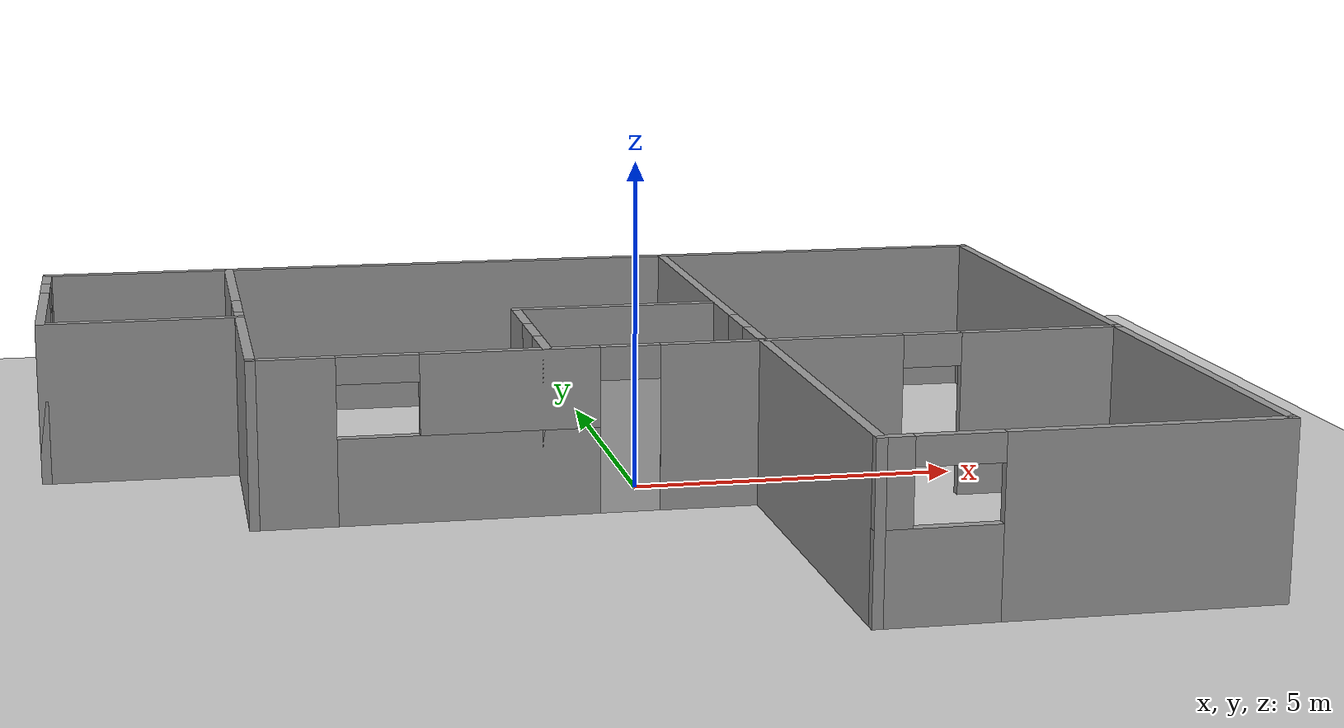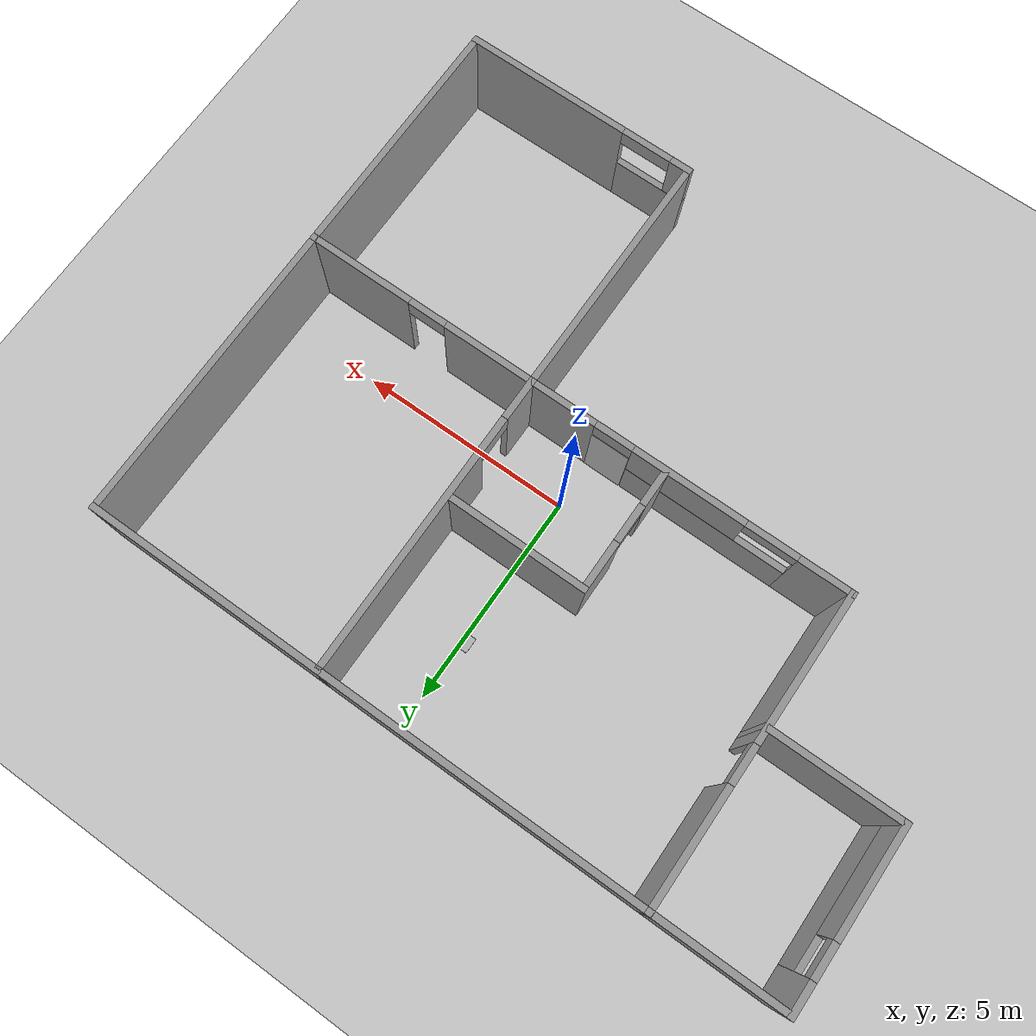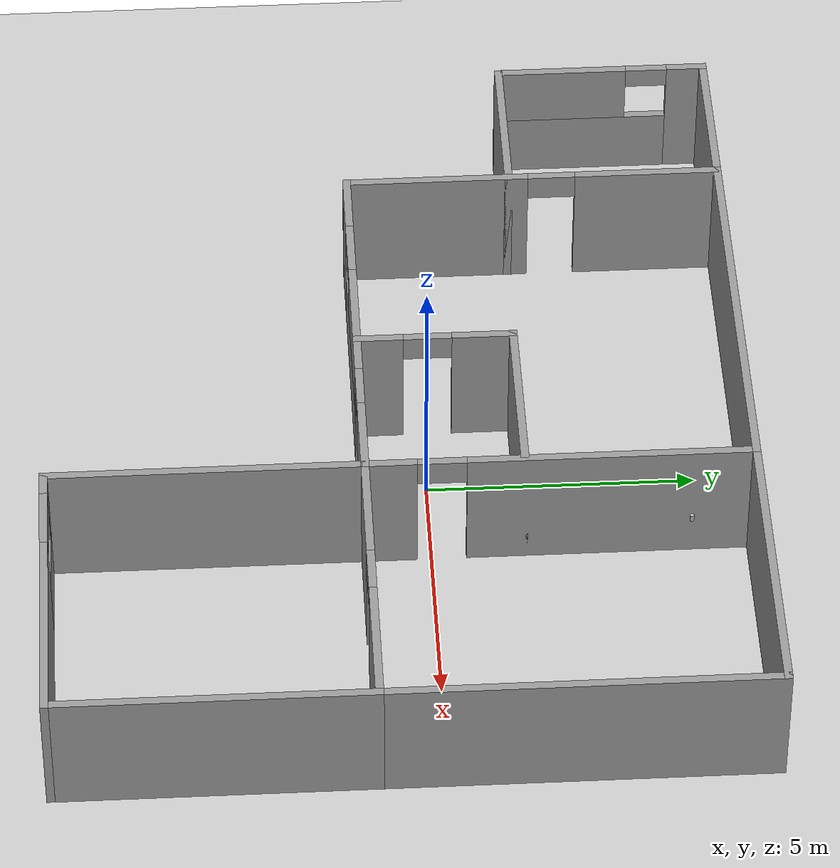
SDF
<sdf version="1.6">
 <world name="default">
  <light name="sun" type="directional">
   <pose>0 0 10 0 -0 0</pose>
   <diffuse>0.8 0.8 0.8 1</diffuse>
   <specular>0.2 0.2 0.2 1</specular>
   <attenuation>
    <range>1000</range>
    <constant>0.9</constant>
    <linear>0.01</linear>
    <quadratic>0.001</quadratic>
   </attenuation>
   <direction>-0.5 0.1 -0.9</direction>
  </light>
  <model name="ground_plane">
   <static>1</static>
   <link name="link">
    <collision name="collision">
     <geometry><plane><normal>0 0 1</normal><size>100 100</size></plane></geometry>
     <surface><friction><ode><mu>100</mu><mu2>50</mu2></ode></friction></surface>
    </collision>
    <visual name="visual">
     <cast_shadows>0</cast_shadows>
     <geometry><plane><normal>0 0 1</normal><size>100 100</size></plane></geometry>
     <material>
      <script><uri>file://media/materials/scripts/gazebo.material</uri><name>Gazebo/Grey</name></script>
     </material>
    </visual>
   </link>
  </model>
  <gravity>0 0 -9.8</gravity>
  <magnetic_field>6e-06 2.3e-05 -4.2e-05</magnetic_field>
  <atmosphere type="adiabatic"/>
  <physics name="default_physics" default="0" type="ode">
   <max_step_size>0.001</max_step_size>
   <real_time_factor>1</real_time_factor>
   <real_time_update_rate>1000</real_time_update_rate>
  </physics>
  <scene><ambient>0.4 0.4 0.4 1</ambient><background>0.7 0.7 0.7 1</background><shadows>1</shadows></scene>
  <spherical_coordinates>
   <surface_model>EARTH_WGS84</surface_model>
   <latitude_deg>0</latitude_deg>
   <longitude_deg>0</longitude_deg>
   <elevation>0</elevation>
   <heading_deg>0</heading_deg>
  </spherical_coordinates>
  <model name="House">
   <link name="Wall_100">
    <pose>0.885 2.25 0 0 -0 0</pose>
    <visual name="Wall_100_Visual">
     <pose>0 0 1.25 0 -0 0</pose>
     <geometry><box><size>3.38 0.15 2.5</size></box></geometry>
     <material>
      <script><uri>file://media/materials/scripts/gazebo.material</uri><name>Gazebo/Grey</name></script>
      <ambient>1 1 1 1</ambient>
      <shader type="pixel"/>
      <diffuse>0.7 0.7 0.7 1</diffuse>
      <specular>0.01 0.01 0.01 1</specular>
      <emissive>0 0 0 1</emissive>
     </material>
     <meta><layer>0</layer></meta>
    </visual>
    <collision name="Wall_100_Collision">
     <pose>0 0 1.25 0 -0 0</pose>
     <geometry><box><size>3.38 0.15 2.5</size></box></geometry>
     <surface>
      <friction>
       <ode><mu>1</mu><mu2>1</mu2><fdir1>0 0 0</fdir1><slip1>0</slip1><slip2>0</slip2></ode>
       <torsional>
        <coefficient>1</coefficient>
        <patch_radius>0</patch_radius>
        <surface_radius>0</surface_radius>
        <use_patch_radius>1</use_patch_radius>
        <ode><slip>0</slip></ode>
       </torsional>
      </friction>
      <bounce><restitution_coefficient>0</restitution_coefficient><threshold>1e+06</threshold></bounce>
      <contact>
       <collide_without_contact>0</collide_without_contact>
       <collide_without_contact_bitmask>1</collide_without_contact_bitmask>
       <collide_bitmask>1</collide_bitmask>
       <ode>
        <soft_cfm>0</soft_cfm>
        <soft_erp>0.2</soft_erp>
        <kp>1e+13</kp>
        <kd>1</kd>
        <max_vel>0.01</max_vel>
        <min_depth>0</min_depth>
       </ode>
       <bullet>
        <split_impulse>1</split_impulse>
        <split_impulse_penetration_threshold>-0.01</split_impulse_penetration_threshold>
        <soft_cfm>0</soft_cfm>
        <soft_erp>0.2</soft_erp>
        <kp>1e+13</kp>
        <kd>1</kd>
       </bullet>
      </contact>
     </surface>
    </collision>
   </link>
   <link name="Wall_103">
    <pose>-6.5 6.45 0 0 -0 3.14159</pose>
    <visual name="Wall_103_Visual">
     <pose>0 0 1.25 0 -0 0</pose>
     <geometry><box><size>3.15 0.15 2.5</size></box></geometry>
     <material>
      <script><uri>file://media/materials/scripts/gazebo.material</uri><name>Gazebo/Grey</name></script>
      <ambient>1 1 1 1</ambient>
      <shader type="pixel"/>
      <diffuse>0.7 0.7 0.7 1</diffuse>
      <specular>0.01 0.01 0.01 1</specular>
      <emissive>0 0 0 1</emissive>
     </material>
     <meta><layer>0</layer></meta>
    </visual>
    <collision name="Wall_103_Collision">
     <pose>0 0 1.25 0 -0 0</pose>
     <geometry><box><size>3.15 0.15 2.5</size></box></geometry>
     <surface>
      <friction>
       <ode><mu>1</mu><mu2>1</mu2><fdir1>0 0 0</fdir1><slip1>0</slip1><slip2>0</slip2></ode>
       <torsional>
        <coefficient>1</coefficient>
        <patch_radius>0</patch_radius>
        <surface_radius>0</surface_radius>
        <use_patch_radius>1</use_patch_radius>
        <ode><slip>0</slip></ode>
       </torsional>
      </friction>
      <bounce><restitution_coefficient>0</restitution_coefficient><threshold>1e+06</threshold></bounce>
      <contact>
       <collide_without_contact>0</collide_without_contact>
       <collide_without_contact_bitmask>1</collide_without_contact_bitmask>
       <collide_bitmask>1</collide_bitmask>
       <ode>
        <soft_cfm>0</soft_cfm>
        <soft_erp>0.2</soft_erp>
        <kp>1e+13</kp>
        <kd>1</kd>
        <max_vel>0.01</max_vel>
        <min_depth>0</min_depth>
       </ode>
       <bullet>
        <split_impulse>1</split_impulse>
        <split_impulse_penetration_threshold>-0.01</split_impulse_penetration_threshold>
        <soft_cfm>0</soft_cfm>
        <soft_erp>0.2</soft_erp>
        <kp>1e+13</kp>
        <kd>1</kd>
       </bullet>
      </contact>
     </surface>
    </collision>
   </link>
   <link name="Wall_107">
    <pose>-8 4.45 0 0 0 -1.5708</pose>
    <visual name="Wall_107_Visual_0">
     <pose>-1.68247 0 1.25 0 -0 0</pose>
     <geometry><box><size>0.785055 0.15 2.5</size></box></geometry>
     <material>
      <script><uri>file://media/materials/scripts/gazebo.material</uri><name>Gazebo/Grey</name></script>
      <ambient>1 1 1 1</ambient>
      <shader type="pixel"/>
      <diffuse>0.7 0.7 0.7 1</diffuse>
      <specular>0.01 0.01 0.01 1</specular>
      <emissive>0 0 0 1</emissive>
     </material>
     <meta><layer>0</layer></meta>
    </visual>
    <visual name="Wall_107_Visual_1">
     <pose>0.392528 0 0.65 0 -0 0</pose>
     <geometry><box><size>3.36495 0.15 1.3</size></box></geometry>
     <material>
      <script><uri>file://media/materials/scripts/gazebo.material</uri><name>Gazebo/Grey</name></script>
      <ambient>1 1 1 1</ambient>
      <shader type="pixel"/>
      <diffuse>0.7 0.7 0.7 1</diffuse>
      <specular>0.01 0.01 0.01 1</specular>
      <emissive>0 0 0 1</emissive>
     </material>
     <meta><layer>0</layer></meta>
    </visual>
    <visual name="Wall_107_Visual_2">
     <pose>0.792528 0 1.9 0 -0 0</pose>
     <geometry><box><size>2.56494 0.15 1.2</size></box></geometry>
     <material>
      <script><uri>file://media/materials/scripts/gazebo.material</uri><name>Gazebo/Grey</name></script>
      <ambient>1 1 1 1</ambient>
      <shader type="pixel"/>
      <diffuse>0.7 0.7 0.7 1</diffuse>
      <specular>0.01 0.01 0.01 1</specular>
      <emissive>0 0 0 1</emissive>
     </material>
     <meta><layer>0</layer></meta>
    </visual>
    <visual name="Wall_107_Visual_3">
     <pose>-0.889945 0 2.3 0 -0 0</pose>
     <geometry><box><size>0.8 0.15 0.4</size></box></geometry>
     <material>
      <script><uri>file://media/materials/scripts/gazebo.material</uri><name>Gazebo/Grey</name></script>
      <ambient>1 1 1 1</ambient>
      <shader type="pixel"/>
      <diffuse>0.7 0.7 0.7 1</diffuse>
      <specular>0.01 0.01 0.01 1</specular>
      <emissive>0 0 0 1</emissive>
     </material>
     <meta><layer>0</layer></meta>
    </visual>
    <collision name="Wall_107_Collision_0">
     <pose>-1.68247 0 1.25 0 -0 0</pose>
     <geometry><box><size>0.785055 0.15 2.5</size></box></geometry>
     <surface>
      <friction>
       <ode><mu>1</mu><mu2>1</mu2><fdir1>0 0 0</fdir1><slip1>0</slip1><slip2>0</slip2></ode>
       <torsional>
        <coefficient>1</coefficient>
        <patch_radius>0</patch_radius>
        <surface_radius>0</surface_radius>
        <use_patch_radius>1</use_patch_radius>
        <ode><slip>0</slip></ode>
       </torsional>
      </friction>
      <bounce><restitution_coefficient>0</restitution_coefficient><threshold>1e+06</threshold></bounce>
      <contact>
       <collide_without_contact>0</collide_without_contact>
       <collide_without_contact_bitmask>1</collide_without_contact_bitmask>
       <collide_bitmask>1</collide_bitmask>
       <ode>
        <soft_cfm>0</soft_cfm>
        <soft_erp>0.2</soft_erp>
        <kp>1e+13</kp>
        <kd>1</kd>
        <max_vel>0.01</max_vel>
        <min_depth>0</min_depth>
       </ode>
       <bullet>
        <split_impulse>1</split_impulse>
        <split_impulse_penetration_threshold>-0.01</split_impulse_penetration_threshold>
        <soft_cfm>0</soft_cfm>
        <soft_erp>0.2</soft_erp>
        <kp>1e+13</kp>
        <kd>1</kd>
       </bullet>
      </contact>
     </surface>
    </collision>
    <collision name="Wall_107_Collision_1">
     <pose>0.392528 0 0.65 0 -0 0</pose>
     <geometry><box><size>3.36495 0.15 1.3</size></box></geometry>
     <surface>
      <friction>
       <ode><mu>1</mu><mu2>1</mu2><fdir1>0 0 0</fdir1><slip1>0</slip1><slip2>0</slip2></ode>
       <torsional>
        <coefficient>1</coefficient>
        <patch_radius>0</patch_radius>
        <surface_radius>0</surface_radius>
        <use_patch_radius>1</use_patch_radius>
        <ode><slip>0</slip></ode>
       </torsional>
      </friction>
      <bounce><restitution_coefficient>0</restitution_coefficient><threshold>1e+06</threshold></bounce>
      <contact>
       <collide_without_contact>0</collide_without_contact>
       <collide_without_contact_bitmask>1</collide_without_contact_bitmask>
       <collide_bitmask>1</collide_bitmask>
       <ode>
        <soft_cfm>0</soft_cfm>
        <soft_erp>0.2</soft_erp>
        <kp>1e+13</kp>
        <kd>1</kd>
        <max_vel>0.01</max_vel>
        <min_depth>0</min_depth>
       </ode>
       <bullet>
        <split_impulse>1</split_impulse>
        <split_impulse_penetration_threshold>-0.01</split_impulse_penetration_threshold>
        <soft_cfm>0</soft_cfm>
        <soft_erp>0.2</soft_erp>
        <kp>1e+13</kp>
        <kd>1</kd>
       </bullet>
      </contact>
     </surface>
    </collision>
    <collision name="Wall_107_Collision_2">
     <pose>0.792528 0 1.9 0 -0 0</pose>
     <geometry><box><size>2.56494 0.15 1.2</size></box></geometry>
     <surface>
      <friction>
       <ode><mu>1</mu><mu2>1</mu2><fdir1>0 0 0</fdir1><slip1>0</slip1><slip2>0</slip2></ode>
       <torsional>
        <coefficient>1</coefficient>
        <patch_radius>0</patch_radius>
        <surface_radius>0</surface_radius>
        <use_patch_radius>1</use_patch_radius>
        <ode><slip>0</slip></ode>
       </torsional>
      </friction>
      <bounce><restitution_coefficient>0</restitution_coefficient><threshold>1e+06</threshold></bounce>
      <contact>
       <collide_without_contact>0</collide_without_contact>
       <collide_without_contact_bitmask>1</collide_without_contact_bitmask>
       <collide_bitmask>1</collide_bitmask>
       <ode>
        <soft_cfm>0</soft_cfm>
        <soft_erp>0.2</soft_erp>
        <kp>1e+13</kp>
        <kd>1</kd>
        <max_vel>0.01</max_vel>
        <min_depth>0</min_depth>
       </ode>
       <bullet>
        <split_impulse>1</split_impulse>
        <split_impulse_penetration_threshold>-0.01</split_impulse_penetration_threshold>
        <soft_cfm>0</soft_cfm>
        <soft_erp>0.2</soft_erp>
        <kp>1e+13</kp>
        <kd>1</kd>
       </bullet>
      </contact>
     </surface>
    </collision>
    <collision name="Wall_107_Collision_3">
     <pose>-0.889945 0 2.3 0 -0 0</pose>
     <geometry><box><size>0.8 0.15 0.4</size></box></geometry>
     <surface>
      <friction>
       <ode><mu>1</mu><mu2>1</mu2><fdir1>0 0 0</fdir1><slip1>0</slip1><slip2>0</slip2></ode>
       <torsional>
        <coefficient>1</coefficient>
        <patch_radius>0</patch_radius>
        <surface_radius>0</surface_radius>
        <use_patch_radius>1</use_patch_radius>
        <ode><slip>0</slip></ode>
       </torsional>
      </friction>
      <bounce><restitution_coefficient>0</restitution_coefficient><threshold>1e+06</threshold></bounce>
      <contact>
       <collide_without_contact>0</collide_without_contact>
       <collide_without_contact_bitmask>1</collide_without_contact_bitmask>
       <collide_bitmask>1</collide_bitmask>
       <ode>
        <soft_cfm>0</soft_cfm>
        <soft_erp>0.2</soft_erp>
        <kp>1e+13</kp>
        <kd>1</kd>
        <max_vel>0.01</max_vel>
        <min_depth>0</min_depth>
       </ode>
       <bullet>
        <split_impulse>1</split_impulse>
        <split_impulse_penetration_threshold>-0.01</split_impulse_penetration_threshold>
        <soft_cfm>0</soft_cfm>
        <soft_erp>0.2</soft_erp>
        <kp>1e+13</kp>
        <kd>1</kd>
       </bullet>
      </contact>
     </surface>
    </collision>
   </link>
   <link name="Wall_109">
    <pose>-6.5 2.45 0 0 -0 0</pose>
    <visual name="Wall_109_Visual">
     <pose>0 0 1.25 0 -0 0</pose>
     <geometry><box><size>3.15 0.15 2.5</size></box></geometry>
     <material>
      <script><uri>file://media/materials/scripts/gazebo.material</uri><name>Gazebo/Grey</name></script>
      <ambient>1 1 1 1</ambient>
      <shader type="pixel"/>
      <diffuse>0.7 0.7 0.7 1</diffuse>
      <specular>0.01 0.01 0.01 1</specular>
      <emissive>0 0 0 1</emissive>
     </material>
     <meta><layer>0</layer></meta>
    </visual>
    <collision name="Wall_109_Collision">
     <pose>0 0 1.25 0 -0 0</pose>
     <geometry><box><size>3.15 0.15 2.5</size></box></geometry>
     <surface>
      <friction>
       <ode><mu>1</mu><mu2>1</mu2><fdir1>0 0 0</fdir1><slip1>0</slip1><slip2>0</slip2></ode>
       <torsional>
        <coefficient>1</coefficient>
        <patch_radius>0</patch_radius>
        <surface_radius>0</surface_radius>
        <use_patch_radius>1</use_patch_radius>
        <ode><slip>0</slip></ode>
       </torsional>
      </friction>
      <bounce><restitution_coefficient>0</restitution_coefficient><threshold>1e+06</threshold></bounce>
      <contact>
       <collide_without_contact>0</collide_without_contact>
       <collide_without_contact_bitmask>1</collide_without_contact_bitmask>
       <collide_bitmask>1</collide_bitmask>
       <ode>
        <soft_cfm>0</soft_cfm>
        <soft_erp>0.2</soft_erp>
        <kp>1e+13</kp>
        <kd>1</kd>
        <max_vel>0.01</max_vel>
        <min_depth>0</min_depth>
       </ode>
       <bullet>
        <split_impulse>1</split_impulse>
        <split_impulse_penetration_threshold>-0.01</split_impulse_penetration_threshold>
        <soft_cfm>0</soft_cfm>
        <soft_erp>0.2</soft_erp>
        <kp>1e+13</kp>
        <kd>1</kd>
       </bullet>
      </contact>
     </surface>
    </collision>
   </link>
   <link name="Wall_77">
    <pose>-1.25 6.45 0 0 -0 0</pose>
    <visual name="Wall_77_Visual">
     <pose>0 0 1.25 0 -0 0</pose>
     <geometry><box><size>7.65 0.15 2.5</size></box></geometry>
     <material>
      <script><uri>file://media/materials/scripts/gazebo.material</uri><name>Gazebo/Grey</name></script>
      <ambient>1 1 1 1</ambient>
      <shader type="pixel"/>
      <diffuse>0.7 0.7 0.7 1</diffuse>
      <specular>0.01 0.01 0.01 1</specular>
      <emissive>0 0 0 1</emissive>
     </material>
     <meta><layer>0</layer></meta>
    </visual>
    <collision name="Wall_77_Collision">
     <pose>0 0 1.25 0 -0 0</pose>
     <geometry><box><size>7.65 0.15 2.5</size></box></geometry>
     <surface>
      <friction>
       <ode><mu>1</mu><mu2>1</mu2><fdir1>0 0 0</fdir1><slip1>0</slip1><slip2>0</slip2></ode>
       <torsional>
        <coefficient>1</coefficient>
        <patch_radius>0</patch_radius>
        <surface_radius>0</surface_radius>
        <use_patch_radius>1</use_patch_radius>
        <ode><slip>0</slip></ode>
       </torsional>
      </friction>
      <bounce><restitution_coefficient>0</restitution_coefficient><threshold>1e+06</threshold></bounce>
      <contact>
       <collide_without_contact>0</collide_without_contact>
       <collide_without_contact_bitmask>1</collide_without_contact_bitmask>
       <collide_bitmask>1</collide_bitmask>
       <ode>
        <soft_cfm>0</soft_cfm>
        <soft_erp>0.2</soft_erp>
        <kp>1e+13</kp>
        <kd>1</kd>
        <max_vel>0.01</max_vel>
        <min_depth>0</min_depth>
       </ode>
       <bullet>
        <split_impulse>1</split_impulse>
        <split_impulse_penetration_threshold>-0.01</split_impulse_penetration_threshold>
        <soft_cfm>0</soft_cfm>
        <soft_erp>0.2</soft_erp>
        <kp>1e+13</kp>
        <kd>1</kd>
       </bullet>
      </contact>
     </surface>
    </collision>
   </link>
   <link name="Wall_79">
    <pose>5.25 6.45 0 0 -0 0</pose>
    <visual name="Wall_79_Visual">
     <pose>0 0 1.25 0 -0 0</pose>
     <geometry><box><size>5.65 0.15 2.5</size></box></geometry>
     <material>
      <script><uri>file://media/materials/scripts/gazebo.material</uri><name>Gazebo/Grey</name></script>
      <ambient>1 1 1 1</ambient>
      <shader type="pixel"/>
      <diffuse>0.7 0.7 0.7 1</diffuse>
      <specular>0.01 0.01 0.01 1</specular>
      <emissive>0 0 0 1</emissive>
     </material>
     <meta><layer>0</layer></meta>
    </visual>
    <collision name="Wall_79_Collision">
     <pose>0 0 1.25 0 -0 0</pose>
     <geometry><box><size>5.65 0.15 2.5</size></box></geometry>
     <surface>
      <friction>
       <ode><mu>1</mu><mu2>1</mu2><fdir1>0 0 0</fdir1><slip1>0</slip1><slip2>0</slip2></ode>
       <torsional>
        <coefficient>1</coefficient>
        <patch_radius>0</patch_radius>
        <surface_radius>0</surface_radius>
        <use_patch_radius>1</use_patch_radius>
        <ode><slip>0</slip></ode>
       </torsional>
      </friction>
      <bounce><restitution_coefficient>0</restitution_coefficient><threshold>1e+06</threshold></bounce>
      <contact>
       <collide_without_contact>0</collide_without_contact>
       <collide_without_contact_bitmask>1</collide_without_contact_bitmask>
       <collide_bitmask>1</collide_bitmask>
       <ode>
        <soft_cfm>0</soft_cfm>
        <soft_erp>0.2</soft_erp>
        <kp>1e+13</kp>
        <kd>1</kd>
        <max_vel>0.01</max_vel>
        <min_depth>0</min_depth>
       </ode>
       <bullet>
        <split_impulse>1</split_impulse>
        <split_impulse_penetration_threshold>-0.01</split_impulse_penetration_threshold>
        <soft_cfm>0</soft_cfm>
        <soft_erp>0.2</soft_erp>
        <kp>1e+13</kp>
        <kd>1</kd>
       </bullet>
      </contact>
     </surface>
    </collision>
   </link>
   <link name="Wall_81">
    <pose>8 2.9 0 0 0 -1.5708</pose>
    <visual name="Wall_81_Visual">
     <pose>0 0 1.25 0 -0 0</pose>
     <geometry><box><size>7.25 0.15 2.5</size></box></geometry>
     <material>
      <script><uri>file://media/materials/scripts/gazebo.material</uri><name>Gazebo/Grey</name></script>
      <ambient>1 1 1 1</ambient>
      <shader type="pixel"/>
      <diffuse>0.7 0.7 0.7 1</diffuse>
      <specular>0.01 0.01 0.01 1</specular>
      <emissive>0 0 0 1</emissive>
     </material>
     <meta><layer>0</layer></meta>
    </visual>
    <collision name="Wall_81_Collision">
     <pose>0 0 1.25 0 -0 0</pose>
     <geometry><box><size>7.25 0.15 2.5</size></box></geometry>
     <surface>
      <friction>
       <ode><mu>1</mu><mu2>1</mu2><fdir1>0 0 0</fdir1><slip1>0</slip1><slip2>0</slip2></ode>
       <torsional>
        <coefficient>1</coefficient>
        <patch_radius>0</patch_radius>
        <surface_radius>0</surface_radius>
        <use_patch_radius>1</use_patch_radius>
        <ode><slip>0</slip></ode>
       </torsional>
      </friction>
      <bounce><restitution_coefficient>0</restitution_coefficient><threshold>1e+06</threshold></bounce>
      <contact>
       <collide_without_contact>0</collide_without_contact>
       <collide_without_contact_bitmask>1</collide_without_contact_bitmask>
       <collide_bitmask>1</collide_bitmask>
       <ode>
        <soft_cfm>0</soft_cfm>
        <soft_erp>0.2</soft_erp>
        <kp>1e+13</kp>
        <kd>1</kd>
        <max_vel>0.01</max_vel>
        <min_depth>0</min_depth>
       </ode>
       <bullet>
        <split_impulse>1</split_impulse>
        <split_impulse_penetration_threshold>-0.01</split_impulse_penetration_threshold>
        <soft_cfm>0</soft_cfm>
        <soft_erp>0.2</soft_erp>
        <kp>1e+13</kp>
        <kd>1</kd>
       </bullet>
      </contact>
     </surface>
    </collision>
   </link>
   <link name="Wall_83">
    <pose>8 -3.55 0 0 0 -1.5708</pose>
    <visual name="Wall_83_Visual">
     <pose>0 0 1.25 0 -0 0</pose>
     <geometry><box><size>5.95 0.15 2.5</size></box></geometry>
     <material>
      <script><uri>file://media/materials/scripts/gazebo.material</uri><name>Gazebo/Grey</name></script>
      <ambient>1 1 1 1</ambient>
      <shader type="pixel"/>
      <diffuse>0.7 0.7 0.7 1</diffuse>
      <specular>0.01 0.01 0.01 1</specular>
      <emissive>0 0 0 1</emissive>
     </material>
     <meta><layer>0</layer></meta>
    </visual>
    <collision name="Wall_83_Collision">
     <pose>0 0 1.25 0 -0 0</pose>
     <geometry><box><size>5.95 0.15 2.5</size></box></geometry>
     <surface>
      <friction>
       <ode><mu>1</mu><mu2>1</mu2><fdir1>0 0 0</fdir1><slip1>0</slip1><slip2>0</slip2></ode>
       <torsional>
        <coefficient>1</coefficient>
        <patch_radius>0</patch_radius>
        <surface_radius>0</surface_radius>
        <use_patch_radius>1</use_patch_radius>
        <ode><slip>0</slip></ode>
       </torsional>
      </friction>
      <bounce><restitution_coefficient>0</restitution_coefficient><threshold>1e+06</threshold></bounce>
      <contact>
       <collide_without_contact>0</collide_without_contact>
       <collide_without_contact_bitmask>1</collide_without_contact_bitmask>
       <collide_bitmask>1</collide_bitmask>
       <ode>
        <soft_cfm>0</soft_cfm>
        <soft_erp>0.2</soft_erp>
        <kp>1e+13</kp>
        <kd>1</kd>
        <max_vel>0.01</max_vel>
        <min_depth>0</min_depth>
       </ode>
       <bullet>
        <split_impulse>1</split_impulse>
        <split_impulse_penetration_threshold>-0.01</split_impulse_penetration_threshold>
        <soft_cfm>0</soft_cfm>
        <soft_erp>0.2</soft_erp>
        <kp>1e+13</kp>
        <kd>1</kd>
       </bullet>
      </contact>
     </surface>
    </collision>
   </link>
   <link name="Wall_85">
    <pose>5.25 -6.45 0 0 -0 3.14159</pose>
    <visual name="Wall_85_Visual_3">
     <pose>1.71326 0 2.3 0 -0 0</pose>
     <geometry><box><size>1.2 0.15 0.4</size></box></geometry>
     <material>
      <script><uri>file://media/materials/scripts/gazebo.material</uri><name>Gazebo/Grey</name></script>
      <ambient>1 1 1 1</ambient>
      <shader type="pixel"/>
      <diffuse>0.7 0.7 0.7 1</diffuse>
      <specular>0.01 0.01 0.01 1</specular>
      <emissive>0 0 0 1</emissive>
     </material>
     <meta><layer>0</layer></meta>
    </visual>
    <visual name="Wall_85_Visual_0">
     <pose>-0.855868 0 1.25 0 -0 0</pose>
     <geometry><box><size>3.93826 0.15 2.5</size></box></geometry>
     <material>
      <script><uri>file://media/materials/scripts/gazebo.material</uri><name>Gazebo/Grey</name></script>
      <ambient>1 1 1 1</ambient>
      <shader type="pixel"/>
      <diffuse>0.7 0.7 0.7 1</diffuse>
      <specular>0.01 0.01 0.01 1</specular>
      <emissive>0 0 0 1</emissive>
     </material>
     <meta><layer>0</layer></meta>
    </visual>
    <visual name="Wall_85_Visual_1">
     <pose>1.96913 0 0.65 0 -0 0</pose>
     <geometry><box><size>1.71174 0.15 1.3</size></box></geometry>
     <material>
      <script><uri>file://media/materials/scripts/gazebo.material</uri><name>Gazebo/Grey</name></script>
      <ambient>1 1 1 1</ambient>
      <shader type="pixel"/>
      <diffuse>0.7 0.7 0.7 1</diffuse>
      <specular>0.01 0.01 0.01 1</specular>
      <emissive>0 0 0 1</emissive>
     </material>
     <meta><layer>0</layer></meta>
    </visual>
    <visual name="Wall_85_Visual_2">
     <pose>2.56913 0 1.9 0 -0 0</pose>
     <geometry><box><size>0.511736 0.15 1.2</size></box></geometry>
     <material>
      <script><uri>file://media/materials/scripts/gazebo.material</uri><name>Gazebo/Grey</name></script>
      <ambient>1 1 1 1</ambient>
      <shader type="pixel"/>
      <diffuse>0.7 0.7 0.7 1</diffuse>
      <specular>0.01 0.01 0.01 1</specular>
      <emissive>0 0 0 1</emissive>
     </material>
     <meta><layer>0</layer></meta>
    </visual>
    <collision name="Wall_85_Collision_0">
     <pose>-0.855868 0 1.25 0 -0 0</pose>
     <geometry><box><size>3.93826 0.15 2.5</size></box></geometry>
     <surface>
      <friction>
       <ode><mu>1</mu><mu2>1</mu2><fdir1>0 0 0</fdir1><slip1>0</slip1><slip2>0</slip2></ode>
       <torsional>
        <coefficient>1</coefficient>
        <patch_radius>0</patch_radius>
        <surface_radius>0</surface_radius>
        <use_patch_radius>1</use_patch_radius>
        <ode><slip>0</slip></ode>
       </torsional>
      </friction>
      <bounce><restitution_coefficient>0</restitution_coefficient><threshold>1e+06</threshold></bounce>
      <contact>
       <collide_without_contact>0</collide_without_contact>
       <collide_without_contact_bitmask>1</collide_without_contact_bitmask>
       <collide_bitmask>1</collide_bitmask>
       <ode>
        <soft_cfm>0</soft_cfm>
        <soft_erp>0.2</soft_erp>
        <kp>1e+13</kp>
        <kd>1</kd>
        <max_vel>0.01</max_vel>
        <min_depth>0</min_depth>
       </ode>
       <bullet>
        <split_impulse>1</split_impulse>
        <split_impulse_penetration_threshold>-0.01</split_impulse_penetration_threshold>
        <soft_cfm>0</soft_cfm>
        <soft_erp>0.2</soft_erp>
        <kp>1e+13</kp>
        <kd>1</kd>
       </bullet>
      </contact>
     </surface>
    </collision>
    <collision name="Wall_85_Collision_1">
     <pose>1.96913 0 0.65 0 -0 0</pose>
     <geometry><box><size>1.71174 0.15 1.3</size></box></geometry>
     <surface>
      <friction>
       <ode><mu>1</mu><mu2>1</mu2><fdir1>0 0 0</fdir1><slip1>0</slip1><slip2>0</slip2></ode>
       <torsional>
        <coefficient>1</coefficient>
        <patch_radius>0</patch_radius>
        <surface_radius>0</surface_radius>
        <use_patch_radius>1</use_patch_radius>
        <ode><slip>0</slip></ode>
       </torsional>
      </friction>
      <bounce><restitution_coefficient>0</restitution_coefficient><threshold>1e+06</threshold></bounce>
      <contact>
       <collide_without_contact>0</collide_without_contact>
       <collide_without_contact_bitmask>1</collide_without_contact_bitmask>
       <collide_bitmask>1</collide_bitmask>
       <ode>
        <soft_cfm>0</soft_cfm>
        <soft_erp>0.2</soft_erp>
        <kp>1e+13</kp>
        <kd>1</kd>
        <max_vel>0.01</max_vel>
        <min_depth>0</min_depth>
       </ode>
       <bullet>
        <split_impulse>1</split_impulse>
        <split_impulse_penetration_threshold>-0.01</split_impulse_penetration_threshold>
        <soft_cfm>0</soft_cfm>
        <soft_erp>0.2</soft_erp>
        <kp>1e+13</kp>
        <kd>1</kd>
       </bullet>
      </contact>
     </surface>
    </collision>
    <collision name="Wall_85_Collision_2">
     <pose>2.56913 0 1.9 0 -0 0</pose>
     <geometry><box><size>0.511736 0.15 1.2</size></box></geometry>
     <surface>
      <friction>
       <ode><mu>1</mu><mu2>1</mu2><fdir1>0 0 0</fdir1><slip1>0</slip1><slip2>0</slip2></ode>
       <torsional>
        <coefficient>1</coefficient>
        <patch_radius>0</patch_radius>
        <surface_radius>0</surface_radius>
        <use_patch_radius>1</use_patch_radius>
        <ode><slip>0</slip></ode>
       </torsional>
      </friction>
      <bounce><restitution_coefficient>0</restitution_coefficient><threshold>1e+06</threshold></bounce>
      <contact>
       <collide_without_contact>0</collide_without_contact>
       <collide_without_contact_bitmask>1</collide_without_contact_bitmask>
       <collide_bitmask>1</collide_bitmask>
       <ode>
        <soft_cfm>0</soft_cfm>
        <soft_erp>0.2</soft_erp>
        <kp>1e+13</kp>
        <kd>1</kd>
        <max_vel>0.01</max_vel>
        <min_depth>0</min_depth>
       </ode>
       <bullet>
        <split_impulse>1</split_impulse>
        <split_impulse_penetration_threshold>-0.01</split_impulse_penetration_threshold>
        <soft_cfm>0</soft_cfm>
        <soft_erp>0.2</soft_erp>
        <kp>1e+13</kp>
        <kd>1</kd>
       </bullet>
      </contact>
     </surface>
    </collision>
    <collision name="Wall_85_Collision_3">
     <pose>1.71326 0 2.3 0 -0 0</pose>
     <geometry><box><size>1.2 0.15 0.4</size></box></geometry>
     <surface>
      <friction>
       <ode><mu>1</mu><mu2>1</mu2><fdir1>0 0 0</fdir1><slip1>0</slip1><slip2>0</slip2></ode>
       <torsional>
        <coefficient>1</coefficient>
        <patch_radius>0</patch_radius>
        <surface_radius>0</surface_radius>
        <use_patch_radius>1</use_patch_radius>
        <ode><slip>0</slip></ode>
       </torsional>
      </friction>
      <bounce><restitution_coefficient>0</restitution_coefficient><threshold>1e+06</threshold></bounce>
      <contact>
       <collide_without_contact>0</collide_without_contact>
       <collide_without_contact_bitmask>1</collide_without_contact_bitmask>
       <collide_bitmask>1</collide_bitmask>
       <ode>
        <soft_cfm>0</soft_cfm>
        <soft_erp>0.2</soft_erp>
        <kp>1e+13</kp>
        <kd>1</kd>
        <max_vel>0.01</max_vel>
        <min_depth>0</min_depth>
       </ode>
       <bullet>
        <split_impulse>1</split_impulse>
        <split_impulse_penetration_threshold>-0.01</split_impulse_penetration_threshold>
        <soft_cfm>0</soft_cfm>
        <soft_erp>0.2</soft_erp>
        <kp>1e+13</kp>
        <kd>1</kd>
       </bullet>
      </contact>
     </surface>
    </collision>
   </link>
   <link name="Wall_87">
    <pose>2.5 -3.55 0 0 -0 1.5708</pose>
    <visual name="Wall_87_Visual">
     <pose>0 0 1.25 0 -0 0</pose>
     <geometry><box><size>5.95 0.15 2.5</size></box></geometry>
     <material>
      <script><uri>file://media/materials/scripts/gazebo.material</uri><name>Gazebo/Grey</name></script>
      <ambient>1 1 1 1</ambient>
      <shader type="pixel"/>
      <diffuse>0.7 0.7 0.7 1</diffuse>
      <specular>0.01 0.01 0.01 1</specular>
      <emissive>0 0 0 1</emissive>
     </material>
     <meta><layer>0</layer></meta>
    </visual>
    <collision name="Wall_87_Collision">
     <pose>0 0 1.25 0 -0 0</pose>
     <geometry><box><size>5.95 0.15 2.5</size></box></geometry>
     <surface>
      <friction>
       <ode><mu>1</mu><mu2>1</mu2><fdir1>0 0 0</fdir1><slip1>0</slip1><slip2>0</slip2></ode>
       <torsional>
        <coefficient>1</coefficient>
        <patch_radius>0</patch_radius>
        <surface_radius>0</surface_radius>
        <use_patch_radius>1</use_patch_radius>
        <ode><slip>0</slip></ode>
       </torsional>
      </friction>
      <bounce><restitution_coefficient>0</restitution_coefficient><threshold>1e+06</threshold></bounce>
      <contact>
       <collide_without_contact>0</collide_without_contact>
       <collide_without_contact_bitmask>1</collide_without_contact_bitmask>
       <collide_bitmask>1</collide_bitmask>
       <ode>
        <soft_cfm>0</soft_cfm>
        <soft_erp>0.2</soft_erp>
        <kp>1e+13</kp>
        <kd>1</kd>
        <max_vel>0.01</max_vel>
        <min_depth>0</min_depth>
       </ode>
       <bullet>
        <split_impulse>1</split_impulse>
        <split_impulse_penetration_threshold>-0.01</split_impulse_penetration_threshold>
        <soft_cfm>0</soft_cfm>
        <soft_erp>0.2</soft_erp>
        <kp>1e+13</kp>
        <kd>1</kd>
       </bullet>
      </contact>
     </surface>
    </collision>
   </link>
   <link name="Wall_89">
    <pose>5.25 -0.65 0 0 -0 0</pose>
    <visual name="Wall_89_Visual_0">
     <pose>-1.72046 0 1.25 0 -0 0</pose>
     <geometry><box><size>2.20908 0.15 2.5</size></box></geometry>
     <material>
      <script><uri>file://media/materials/scripts/gazebo.material</uri><name>Gazebo/Grey</name></script>
      <ambient>1 1 1 1</ambient>
      <shader type="pixel"/>
      <diffuse>0.7 0.7 0.7 1</diffuse>
      <specular>0.01 0.01 0.01 1</specular>
      <emissive>0 0 0 1</emissive>
     </material>
     <meta><layer>0</layer></meta>
    </visual>
    <visual name="Wall_89_Visual_1">
     <pose>1.55454 0 1.25 0 -0 0</pose>
     <geometry><box><size>2.54092 0.15 2.5</size></box></geometry>
     <material>
      <script><uri>file://media/materials/scripts/gazebo.material</uri><name>Gazebo/Grey</name></script>
      <ambient>1 1 1 1</ambient>
      <shader type="pixel"/>
      <diffuse>0.7 0.7 0.7 1</diffuse>
      <specular>0.01 0.01 0.01 1</specular>
      <emissive>0 0 0 1</emissive>
     </material>
     <meta><layer>0</layer></meta>
    </visual>
    <visual name="Wall_89_Visual_2">
     <pose>-0.165924 0 2.25 0 -0 0</pose>
     <geometry><box><size>0.9 0.15 0.5</size></box></geometry>
     <material>
      <script><uri>file://media/materials/scripts/gazebo.material</uri><name>Gazebo/Grey</name></script>
      <ambient>1 1 1 1</ambient>
      <shader type="pixel"/>
      <diffuse>0.7 0.7 0.7 1</diffuse>
      <specular>0.01 0.01 0.01 1</specular>
      <emissive>0 0 0 1</emissive>
     </material>
     <meta><layer>0</layer></meta>
    </visual>
    <collision name="Wall_89_Collision_0">
     <pose>-1.72046 0 1.25 0 -0 0</pose>
     <geometry><box><size>2.20908 0.15 2.5</size></box></geometry>
     <surface>
      <friction>
       <ode><mu>1</mu><mu2>1</mu2><fdir1>0 0 0</fdir1><slip1>0</slip1><slip2>0</slip2></ode>
       <torsional>
        <coefficient>1</coefficient>
        <patch_radius>0</patch_radius>
        <surface_radius>0</surface_radius>
        <use_patch_radius>1</use_patch_radius>
        <ode><slip>0</slip></ode>
       </torsional>
      </friction>
      <bounce><restitution_coefficient>0</restitution_coefficient><threshold>1e+06</threshold></bounce>
      <contact>
       <collide_without_contact>0</collide_without_contact>
       <collide_without_contact_bitmask>1</collide_without_contact_bitmask>
       <collide_bitmask>1</collide_bitmask>
       <ode>
        <soft_cfm>0</soft_cfm>
        <soft_erp>0.2</soft_erp>
        <kp>1e+13</kp>
        <kd>1</kd>
        <max_vel>0.01</max_vel>
        <min_depth>0</min_depth>
       </ode>
       <bullet>
        <split_impulse>1</split_impulse>
        <split_impulse_penetration_threshold>-0.01</split_impulse_penetration_threshold>
        <soft_cfm>0</soft_cfm>
        <soft_erp>0.2</soft_erp>
        <kp>1e+13</kp>
        <kd>1</kd>
       </bullet>
      </contact>
     </surface>
    </collision>
    <collision name="Wall_89_Collision_1">
     <pose>1.55454 0 1.25 0 -0 0</pose>
     <geometry><box><size>2.54092 0.15 2.5</size></box></geometry>
     <surface>
      <friction>
       <ode><mu>1</mu><mu2>1</mu2><fdir1>0 0 0</fdir1><slip1>0</slip1><slip2>0</slip2></ode>
       <torsional>
        <coefficient>1</coefficient>
        <patch_radius>0</patch_radius>
        <surface_radius>0</surface_radius>
        <use_patch_radius>1</use_patch_radius>
        <ode><slip>0</slip></ode>
       </torsional>
      </friction>
      <bounce><restitution_coefficient>0</restitution_coefficient><threshold>1e+06</threshold></bounce>
      <contact>
       <collide_without_contact>0</collide_without_contact>
       <collide_without_contact_bitmask>1</collide_without_contact_bitmask>
       <collide_bitmask>1</collide_bitmask>
       <ode>
        <soft_cfm>0</soft_cfm>
        <soft_erp>0.2</soft_erp>
        <kp>1e+13</kp>
        <kd>1</kd>
        <max_vel>0.01</max_vel>
        <min_depth>0</min_depth>
       </ode>
       <bullet>
        <split_impulse>1</split_impulse>
        <split_impulse_penetration_threshold>-0.01</split_impulse_penetration_threshold>
        <soft_cfm>0</soft_cfm>
        <soft_erp>0.2</soft_erp>
        <kp>1e+13</kp>
        <kd>1</kd>
       </bullet>
      </contact>
     </surface>
    </collision>
    <collision name="Wall_89_Collision_2">
     <pose>-0.165924 0 2.25 0 -0 0</pose>
     <geometry><box><size>0.9 0.15 0.5</size></box></geometry>
     <surface>
      <friction>
       <ode><mu>1</mu><mu2>1</mu2><fdir1>0 0 0</fdir1><slip1>0</slip1><slip2>0</slip2></ode>
       <torsional>
        <coefficient>1</coefficient>
        <patch_radius>0</patch_radius>
        <surface_radius>0</surface_radius>
        <use_patch_radius>1</use_patch_radius>
        <ode><slip>0</slip></ode>
       </torsional>
      </friction>
      <bounce><restitution_coefficient>0</restitution_coefficient><threshold>1e+06</threshold></bounce>
      <contact>
       <collide_without_contact>0</collide_without_contact>
       <collide_without_contact_bitmask>1</collide_without_contact_bitmask>
       <collide_bitmask>1</collide_bitmask>
       <ode>
        <soft_cfm>0</soft_cfm>
        <soft_erp>0.2</soft_erp>
        <kp>1e+13</kp>
        <kd>1</kd>
        <max_vel>0.01</max_vel>
        <min_depth>0</min_depth>
       </ode>
       <bullet>
        <split_impulse>1</split_impulse>
        <split_impulse_penetration_threshold>-0.01</split_impulse_penetration_threshold>
        <soft_cfm>0</soft_cfm>
        <soft_erp>0.2</soft_erp>
        <kp>1e+13</kp>
        <kd>1</kd>
       </bullet>
      </contact>
     </surface>
    </collision>
   </link>
   <link name="Wall_91">
    <pose>2.5 2.9 0 0 -0 1.5708</pose>
    <visual name="Wall_91_Visual_0">
     <pose>-3.11155 0 1.25 0 -0 0</pose>
     <geometry><box><size>1.0269 0.15 2.5</size></box></geometry>
     <material>
      <script><uri>file://media/materials/scripts/gazebo.material</uri><name>Gazebo/Grey</name></script>
      <ambient>1 1 1 1</ambient>
      <shader type="pixel"/>
      <diffuse>0.7 0.7 0.7 1</diffuse>
      <specular>0.01 0.01 0.01 1</specular>
      <emissive>0 0 0 1</emissive>
     </material>
     <meta><layer>0</layer></meta>
    </visual>
    <visual name="Wall_91_Visual_1">
     <pose>0.96345 0 1.25 0 -0 0</pose>
     <geometry><box><size>5.3231 0.15 2.5</size></box></geometry>
     <material>
      <script><uri>file://media/materials/scripts/gazebo.material</uri><name>Gazebo/Grey</name></script>
      <ambient>1 1 1 1</ambient>
      <shader type="pixel"/>
      <diffuse>0.7 0.7 0.7 1</diffuse>
      <specular>0.01 0.01 0.01 1</specular>
      <emissive>0 0 0 1</emissive>
     </material>
     <meta><layer>0</layer></meta>
    </visual>
    <visual name="Wall_91_Visual_2">
     <pose>-2.1481 0 2.25 0 -0 0</pose>
     <geometry><box><size>0.9 0.15 0.5</size></box></geometry>
     <material>
      <script><uri>file://media/materials/scripts/gazebo.material</uri><name>Gazebo/Grey</name></script>
      <ambient>1 1 1 1</ambient>
      <shader type="pixel"/>
      <diffuse>0.7 0.7 0.7 1</diffuse>
      <specular>0.01 0.01 0.01 1</specular>
      <emissive>0 0 0 1</emissive>
     </material>
     <meta><layer>0</layer></meta>
    </visual>
    <collision name="Wall_91_Collision_0">
     <pose>-3.11155 0 1.25 0 -0 0</pose>
     <geometry><box><size>1.0269 0.15 2.5</size></box></geometry>
     <surface>
      <friction>
       <ode><mu>1</mu><mu2>1</mu2><fdir1>0 0 0</fdir1><slip1>0</slip1><slip2>0</slip2></ode>
       <torsional>
        <coefficient>1</coefficient>
        <patch_radius>0</patch_radius>
        <surface_radius>0</surface_radius>
        <use_patch_radius>1</use_patch_radius>
        <ode><slip>0</slip></ode>
       </torsional>
      </friction>
      <bounce><restitution_coefficient>0</restitution_coefficient><threshold>1e+06</threshold></bounce>
      <contact>
       <collide_without_contact>0</collide_without_contact>
       <collide_without_contact_bitmask>1</collide_without_contact_bitmask>
       <collide_bitmask>1</collide_bitmask>
       <ode>
        <soft_cfm>0</soft_cfm>
        <soft_erp>0.2</soft_erp>
        <kp>1e+13</kp>
        <kd>1</kd>
        <max_vel>0.01</max_vel>
        <min_depth>0</min_depth>
       </ode>
       <bullet>
        <split_impulse>1</split_impulse>
        <split_impulse_penetration_threshold>-0.01</split_impulse_penetration_threshold>
        <soft_cfm>0</soft_cfm>
        <soft_erp>0.2</soft_erp>
        <kp>1e+13</kp>
        <kd>1</kd>
       </bullet>
      </contact>
     </surface>
    </collision>
    <collision name="Wall_91_Collision_2">
     <pose>-2.1481 0 2.25 0 -0 0</pose>
     <geometry><box><size>0.9 0.15 0.5</size></box></geometry>
     <surface>
      <friction>
       <ode><mu>1</mu><mu2>1</mu2><fdir1>0 0 0</fdir1><slip1>0</slip1><slip2>0</slip2></ode>
       <torsional>
        <coefficient>1</coefficient>
        <patch_radius>0</patch_radius>
        <surface_radius>0</surface_radius>
        <use_patch_radius>1</use_patch_radius>
        <ode><slip>0</slip></ode>
       </torsional>
      </friction>
      <bounce><restitution_coefficient>0</restitution_coefficient><threshold>1e+06</threshold></bounce>
      <contact>
       <collide_without_contact>0</collide_without_contact>
       <collide_without_contact_bitmask>1</collide_without_contact_bitmask>
       <collide_bitmask>1</collide_bitmask>
       <ode>
        <soft_cfm>0</soft_cfm>
        <soft_erp>0.2</soft_erp>
        <kp>1e+13</kp>
        <kd>1</kd>
        <max_vel>0.01</max_vel>
        <min_depth>0</min_depth>
       </ode>
       <bullet>
        <split_impulse>1</split_impulse>
        <split_impulse_penetration_threshold>-0.01</split_impulse_penetration_threshold>
        <soft_cfm>0</soft_cfm>
        <soft_erp>0.2</soft_erp>
        <kp>1e+13</kp>
        <kd>1</kd>
       </bullet>
      </contact>
     </surface>
    </collision>
    <collision name="Wall_91_Collision_1">
     <pose>0.96345 0 1.25 0 -0 0</pose>
     <geometry><box><size>5.3231 0.15 2.5</size></box></geometry>
     <surface>
      <friction>
       <ode><mu>1</mu><mu2>1</mu2><fdir1>0 0 0</fdir1><slip1>0</slip1><slip2>0</slip2></ode>
       <torsional>
        <coefficient>1</coefficient>
        <patch_radius>0</patch_radius>
        <surface_radius>0</surface_radius>
        <use_patch_radius>1</use_patch_radius>
        <ode><slip>0</slip></ode>
       </torsional>
      </friction>
      <bounce><restitution_coefficient>0</restitution_coefficient><threshold>1e+06</threshold></bounce>
      <contact>
       <collide_without_contact>0</collide_without_contact>
       <collide_without_contact_bitmask>1</collide_without_contact_bitmask>
       <collide_bitmask>1</collide_bitmask>
       <ode>
        <soft_cfm>0</soft_cfm>
        <soft_erp>0.2</soft_erp>
        <kp>1e+13</kp>
        <kd>1</kd>
        <max_vel>0.01</max_vel>
        <min_depth>0</min_depth>
       </ode>
       <bullet>
        <split_impulse>1</split_impulse>
        <split_impulse_penetration_threshold>-0.01</split_impulse_penetration_threshold>
        <soft_cfm>0</soft_cfm>
        <soft_erp>0.2</soft_erp>
        <kp>1e+13</kp>
        <kd>1</kd>
       </bullet>
      </contact>
     </surface>
    </collision>
   </link>
   <link name="Wall_93">
    <pose>-5 2.9 0 0 0 -1.5708</pose>
    <visual name="Wall_93_Visual_0">
     <pose>-2.22291 0 1.25 0 -0 0</pose>
     <geometry><box><size>2.80417 0.15 2.5</size></box></geometry>
     <material>
      <script><uri>file://media/materials/scripts/gazebo.material</uri><name>Gazebo/Grey</name></script>
      <ambient>1 1 1 1</ambient>
      <shader type="pixel"/>
      <diffuse>0.7 0.7 0.7 1</diffuse>
      <specular>0.01 0.01 0.01 1</specular>
      <emissive>0 0 0 1</emissive>
     </material>
     <meta><layer>0</layer></meta>
    </visual>
    <visual name="Wall_93_Visual_1">
     <pose>1.85209 0 1.25 0 -0 0</pose>
     <geometry><box><size>3.54583 0.15 2.5</size></box></geometry>
     <material>
      <script><uri>file://media/materials/scripts/gazebo.material</uri><name>Gazebo/Grey</name></script>
      <ambient>1 1 1 1</ambient>
      <shader type="pixel"/>
      <diffuse>0.7 0.7 0.7 1</diffuse>
      <specular>0.01 0.01 0.01 1</specular>
      <emissive>0 0 0 1</emissive>
     </material>
     <meta><layer>0</layer></meta>
    </visual>
    <visual name="Wall_93_Visual_2">
     <pose>-0.370826 0 2.25 0 -0 0</pose>
     <geometry><box><size>0.9 0.15 0.5</size></box></geometry>
     <material>
      <script><uri>file://media/materials/scripts/gazebo.material</uri><name>Gazebo/Grey</name></script>
      <ambient>1 1 1 1</ambient>
      <shader type="pixel"/>
      <diffuse>0.7 0.7 0.7 1</diffuse>
      <specular>0.01 0.01 0.01 1</specular>
      <emissive>0 0 0 1</emissive>
     </material>
     <meta><layer>0</layer></meta>
    </visual>
    <collision name="Wall_93_Collision_0">
     <pose>-2.22291 0 1.25 0 -0 0</pose>
     <geometry><box><size>2.80417 0.15 2.5</size></box></geometry>
     <surface>
      <friction>
       <ode><mu>1</mu><mu2>1</mu2><fdir1>0 0 0</fdir1><slip1>0</slip1><slip2>0</slip2></ode>
       <torsional>
        <coefficient>1</coefficient>
        <patch_radius>0</patch_radius>
        <surface_radius>0</surface_radius>
        <use_patch_radius>1</use_patch_radius>
        <ode><slip>0</slip></ode>
       </torsional>
      </friction>
      <bounce><restitution_coefficient>0</restitution_coefficient><threshold>1e+06</threshold></bounce>
      <contact>
       <collide_without_contact>0</collide_without_contact>
       <collide_without_contact_bitmask>1</collide_without_contact_bitmask>
       <collide_bitmask>1</collide_bitmask>
       <ode>
        <soft_cfm>0</soft_cfm>
        <soft_erp>0.2</soft_erp>
        <kp>1e+13</kp>
        <kd>1</kd>
        <max_vel>0.01</max_vel>
        <min_depth>0</min_depth>
       </ode>
       <bullet>
        <split_impulse>1</split_impulse>
        <split_impulse_penetration_threshold>-0.01</split_impulse_penetration_threshold>
        <soft_cfm>0</soft_cfm>
        <soft_erp>0.2</soft_erp>
        <kp>1e+13</kp>
        <kd>1</kd>
       </bullet>
      </contact>
     </surface>
    </collision>
    <collision name="Wall_93_Collision_1">
     <pose>1.85209 0 1.25 0 -0 0</pose>
     <geometry><box><size>3.54583 0.15 2.5</size></box></geometry>
     <surface>
      <friction>
       <ode><mu>1</mu><mu2>1</mu2><fdir1>0 0 0</fdir1><slip1>0</slip1><slip2>0</slip2></ode>
       <torsional>
        <coefficient>1</coefficient>
        <patch_radius>0</patch_radius>
        <surface_radius>0</surface_radius>
        <use_patch_radius>1</use_patch_radius>
        <ode><slip>0</slip></ode>
       </torsional>
      </friction>
      <bounce><restitution_coefficient>0</restitution_coefficient><threshold>1e+06</threshold></bounce>
      <contact>
       <collide_without_contact>0</collide_without_contact>
       <collide_without_contact_bitmask>1</collide_without_contact_bitmask>
       <collide_bitmask>1</collide_bitmask>
       <ode>
        <soft_cfm>0</soft_cfm>
        <soft_erp>0.2</soft_erp>
        <kp>1e+13</kp>
        <kd>1</kd>
        <max_vel>0.01</max_vel>
        <min_depth>0</min_depth>
       </ode>
       <bullet>
        <split_impulse>1</split_impulse>
        <split_impulse_penetration_threshold>-0.01</split_impulse_penetration_threshold>
        <soft_cfm>0</soft_cfm>
        <soft_erp>0.2</soft_erp>
        <kp>1e+13</kp>
        <kd>1</kd>
       </bullet>
      </contact>
     </surface>
    </collision>
    <collision name="Wall_93_Collision_2">
     <pose>-0.370826 0 2.25 0 -0 0</pose>
     <geometry><box><size>0.9 0.15 0.5</size></box></geometry>
     <surface>
      <friction>
       <ode><mu>1</mu><mu2>1</mu2><fdir1>0 0 0</fdir1><slip1>0</slip1><slip2>0</slip2></ode>
       <torsional>
        <coefficient>1</coefficient>
        <patch_radius>0</patch_radius>
        <surface_radius>0</surface_radius>
        <use_patch_radius>1</use_patch_radius>
        <ode><slip>0</slip></ode>
       </torsional>
      </friction>
      <bounce><restitution_coefficient>0</restitution_coefficient><threshold>1e+06</threshold></bounce>
      <contact>
       <collide_without_contact>0</collide_without_contact>
       <collide_without_contact_bitmask>1</collide_without_contact_bitmask>
       <collide_bitmask>1</collide_bitmask>
       <ode>
        <soft_cfm>0</soft_cfm>
        <soft_erp>0.2</soft_erp>
        <kp>1e+13</kp>
        <kd>1</kd>
        <max_vel>0.01</max_vel>
        <min_depth>0</min_depth>
       </ode>
       <bullet>
        <split_impulse>1</split_impulse>
        <split_impulse_penetration_threshold>-0.01</split_impulse_penetration_threshold>
        <soft_cfm>0</soft_cfm>
        <soft_erp>0.2</soft_erp>
        <kp>1e+13</kp>
        <kd>1</kd>
       </bullet>
      </contact>
     </surface>
    </collision>
   </link>
   <link name="Wall_95">
    <pose>-1.25 -0.65 0 0 -0 0</pose>
    <visual name="Wall_95_Visual_0">
     <pose>-3.1837 0 1.25 0 -0 0</pose>
     <geometry><box><size>1.2826 0.15 2.5</size></box></geometry>
     <material>
      <script><uri>file://media/materials/scripts/gazebo.material</uri><name>Gazebo/Grey</name></script>
      <ambient>1 1 1 1</ambient>
      <shader type="pixel"/>
      <diffuse>0.7 0.7 0.7 1</diffuse>
      <specular>0.01 0.01 0.01 1</specular>
      <emissive>0 0 0 1</emissive>
     </material>
     <meta><layer>0</layer></meta>
    </visual>
    <visual name="Wall_95_Visual_1">
     <pose>3.01052 0 1.25 0 -0 0</pose>
     <geometry><box><size>1.62897 0.15 2.5</size></box></geometry>
     <material>
      <script><uri>file://media/materials/scripts/gazebo.material</uri><name>Gazebo/Grey</name></script>
      <ambient>1 1 1 1</ambient>
      <shader type="pixel"/>
      <diffuse>0.7 0.7 0.7 1</diffuse>
      <specular>0.01 0.01 0.01 1</specular>
      <emissive>0 0 0 1</emissive>
     </material>
     <meta><layer>0</layer></meta>
    </visual>
    <visual name="Wall_95_Visual_2">
     <pose>-0.623182 0 0.65 0 -0 0</pose>
     <geometry><box><size>3.83843 0.15 1.3</size></box></geometry>
     <material>
      <script><uri>file://media/materials/scripts/gazebo.material</uri><name>Gazebo/Grey</name></script>
      <ambient>1 1 1 1</ambient>
      <shader type="pixel"/>
      <diffuse>0.7 0.7 0.7 1</diffuse>
      <specular>0.01 0.01 0.01 1</specular>
      <emissive>0 0 0 1</emissive>
     </material>
     <meta><layer>0</layer></meta>
    </visual>
    <visual name="Wall_95_Visual_3">
     <pose>-0.023182 0 1.9 0 -0 0</pose>
     <geometry><box><size>2.63843 0.15 1.2</size></box></geometry>
     <material>
      <script><uri>file://media/materials/scripts/gazebo.material</uri><name>Gazebo/Grey</name></script>
      <ambient>1 1 1 1</ambient>
      <shader type="pixel"/>
      <diffuse>0.7 0.7 0.7 1</diffuse>
      <specular>0.01 0.01 0.01 1</specular>
      <emissive>0 0 0 1</emissive>
     </material>
     <meta><layer>0</layer></meta>
    </visual>
    <visual name="Wall_95_Visual_4">
     <pose>1.74603 0 2.25 0 -0 0</pose>
     <geometry><box><size>0.9 0.15 0.5</size></box></geometry>
     <material>
      <script><uri>file://media/materials/scripts/gazebo.material</uri><name>Gazebo/Grey</name></script>
      <ambient>1 1 1 1</ambient>
      <shader type="pixel"/>
      <diffuse>0.7 0.7 0.7 1</diffuse>
      <specular>0.01 0.01 0.01 1</specular>
      <emissive>0 0 0 1</emissive>
     </material>
     <meta><layer>0</layer></meta>
    </visual>
    <visual name="Wall_95_Visual_5">
     <pose>-1.9424 0 2.3 0 -0 0</pose>
     <geometry><box><size>1.2 0.15 0.4</size></box></geometry>
     <material>
      <script><uri>file://media/materials/scripts/gazebo.material</uri><name>Gazebo/Grey</name></script>
      <ambient>1 1 1 1</ambient>
      <shader type="pixel"/>
      <diffuse>0.7 0.7 0.7 1</diffuse>
      <specular>0.01 0.01 0.01 1</specular>
      <emissive>0 0 0 1</emissive>
     </material>
     <meta><layer>0</layer></meta>
    </visual>
    <collision name="Wall_95_Collision_0">
     <pose>-3.1837 0 1.25 0 -0 0</pose>
     <geometry><box><size>1.2826 0.15 2.5</size></box></geometry>
     <surface>
      <friction>
       <ode><mu>1</mu><mu2>1</mu2><fdir1>0 0 0</fdir1><slip1>0</slip1><slip2>0</slip2></ode>
       <torsional>
        <coefficient>1</coefficient>
        <patch_radius>0</patch_radius>
        <surface_radius>0</surface_radius>
        <use_patch_radius>1</use_patch_radius>
        <ode><slip>0</slip></ode>
       </torsional>
      </friction>
      <bounce><restitution_coefficient>0</restitution_coefficient><threshold>1e+06</threshold></bounce>
      <contact>
       <collide_without_contact>0</collide_without_contact>
       <collide_without_contact_bitmask>1</collide_without_contact_bitmask>
       <collide_bitmask>1</collide_bitmask>
       <ode>
        <soft_cfm>0</soft_cfm>
        <soft_erp>0.2</soft_erp>
        <kp>1e+13</kp>
        <kd>1</kd>
        <max_vel>0.01</max_vel>
        <min_depth>0</min_depth>
       </ode>
       <bullet>
        <split_impulse>1</split_impulse>
        <split_impulse_penetration_threshold>-0.01</split_impulse_penetration_threshold>
        <soft_cfm>0</soft_cfm>
        <soft_erp>0.2</soft_erp>
        <kp>1e+13</kp>
        <kd>1</kd>
       </bullet>
      </contact>
     </surface>
    </collision>
    <collision name="Wall_95_Collision_1">
     <pose>3.01052 0 1.25 0 -0 0</pose>
     <geometry><box><size>1.62897 0.15 2.5</size></box></geometry>
     <surface>
      <friction>
       <ode><mu>1</mu><mu2>1</mu2><fdir1>0 0 0</fdir1><slip1>0</slip1><slip2>0</slip2></ode>
       <torsional>
        <coefficient>1</coefficient>
        <patch_radius>0</patch_radius>
        <surface_radius>0</surface_radius>
        <use_patch_radius>1</use_patch_radius>
        <ode><slip>0</slip></ode>
       </torsional>
      </friction>
      <bounce><restitution_coefficient>0</restitution_coefficient><threshold>1e+06</threshold></bounce>
      <contact>
       <collide_without_contact>0</collide_without_contact>
       <collide_without_contact_bitmask>1</collide_without_contact_bitmask>
       <collide_bitmask>1</collide_bitmask>
       <ode>
        <soft_cfm>0</soft_cfm>
        <soft_erp>0.2</soft_erp>
        <kp>1e+13</kp>
        <kd>1</kd>
        <max_vel>0.01</max_vel>
        <min_depth>0</min_depth>
       </ode>
       <bullet>
        <split_impulse>1</split_impulse>
        <split_impulse_penetration_threshold>-0.01</split_impulse_penetration_threshold>
        <soft_cfm>0</soft_cfm>
        <soft_erp>0.2</soft_erp>
        <kp>1e+13</kp>
        <kd>1</kd>
       </bullet>
      </contact>
     </surface>
    </collision>
    <collision name="Wall_95_Collision_2">
     <pose>-0.623182 0 0.65 0 -0 0</pose>
     <geometry><box><size>3.83843 0.15 1.3</size></box></geometry>
     <surface>
      <friction>
       <ode><mu>1</mu><mu2>1</mu2><fdir1>0 0 0</fdir1><slip1>0</slip1><slip2>0</slip2></ode>
       <torsional>
        <coefficient>1</coefficient>
        <patch_radius>0</patch_radius>
        <surface_radius>0</surface_radius>
        <use_patch_radius>1</use_patch_radius>
        <ode><slip>0</slip></ode>
       </torsional>
      </friction>
      <bounce><restitution_coefficient>0</restitution_coefficient><threshold>1e+06</threshold></bounce>
      <contact>
       <collide_without_contact>0</collide_without_contact>
       <collide_without_contact_bitmask>1</collide_without_contact_bitmask>
       <collide_bitmask>1</collide_bitmask>
       <ode>
        <soft_cfm>0</soft_cfm>
        <soft_erp>0.2</soft_erp>
        <kp>1e+13</kp>
        <kd>1</kd>
        <max_vel>0.01</max_vel>
        <min_depth>0</min_depth>
       </ode>
       <bullet>
        <split_impulse>1</split_impulse>
        <split_impulse_penetration_threshold>-0.01</split_impulse_penetration_threshold>
        <soft_cfm>0</soft_cfm>
        <soft_erp>0.2</soft_erp>
        <kp>1e+13</kp>
        <kd>1</kd>
       </bullet>
      </contact>
     </surface>
    </collision>
    <collision name="Wall_95_Collision_3">
     <pose>-0.023182 0 1.9 0 -0 0</pose>
     <geometry><box><size>2.63843 0.15 1.2</size></box></geometry>
     <surface>
      <friction>
       <ode><mu>1</mu><mu2>1</mu2><fdir1>0 0 0</fdir1><slip1>0</slip1><slip2>0</slip2></ode>
       <torsional>
        <coefficient>1</coefficient>
        <patch_radius>0</patch_radius>
        <surface_radius>0</surface_radius>
        <use_patch_radius>1</use_patch_radius>
        <ode><slip>0</slip></ode>
       </torsional>
      </friction>
      <bounce><restitution_coefficient>0</restitution_coefficient><threshold>1e+06</threshold></bounce>
      <contact>
       <collide_without_contact>0</collide_without_contact>
       <collide_without_contact_bitmask>1</collide_without_contact_bitmask>
       <collide_bitmask>1</collide_bitmask>
       <ode>
        <soft_cfm>0</soft_cfm>
        <soft_erp>0.2</soft_erp>
        <kp>1e+13</kp>
        <kd>1</kd>
        <max_vel>0.01</max_vel>
        <min_depth>0</min_depth>
       </ode>
       <bullet>
        <split_impulse>1</split_impulse>
        <split_impulse_penetration_threshold>-0.01</split_impulse_penetration_threshold>
        <soft_cfm>0</soft_cfm>
        <soft_erp>0.2</soft_erp>
        <kp>1e+13</kp>
        <kd>1</kd>
       </bullet>
      </contact>
     </surface>
    </collision>
    <collision name="Wall_95_Collision_4">
     <pose>1.74603 0 2.25 0 -0 0</pose>
     <geometry><box><size>0.9 0.15 0.5</size></box></geometry>
     <surface>
      <friction>
       <ode><mu>1</mu><mu2>1</mu2><fdir1>0 0 0</fdir1><slip1>0</slip1><slip2>0</slip2></ode>
       <torsional>
        <coefficient>1</coefficient>
        <patch_radius>0</patch_radius>
        <surface_radius>0</surface_radius>
        <use_patch_radius>1</use_patch_radius>
        <ode><slip>0</slip></ode>
       </torsional>
      </friction>
      <bounce><restitution_coefficient>0</restitution_coefficient><threshold>1e+06</threshold></bounce>
      <contact>
       <collide_without_contact>0</collide_without_contact>
       <collide_without_contact_bitmask>1</collide_without_contact_bitmask>
       <collide_bitmask>1</collide_bitmask>
       <ode>
        <soft_cfm>0</soft_cfm>
        <soft_erp>0.2</soft_erp>
        <kp>1e+13</kp>
        <kd>1</kd>
        <max_vel>0.01</max_vel>
        <min_depth>0</min_depth>
       </ode>
       <bullet>
        <split_impulse>1</split_impulse>
        <split_impulse_penetration_threshold>-0.01</split_impulse_penetration_threshold>
        <soft_cfm>0</soft_cfm>
        <soft_erp>0.2</soft_erp>
        <kp>1e+13</kp>
        <kd>1</kd>
       </bullet>
      </contact>
     </surface>
    </collision>
    <collision name="Wall_95_Collision_5">
     <pose>-1.9424 0 2.3 0 -0 0</pose>
     <geometry><box><size>1.2 0.15 0.4</size></box></geometry>
     <surface>
      <friction>
       <ode><mu>1</mu><mu2>1</mu2><fdir1>0 0 0</fdir1><slip1>0</slip1><slip2>0</slip2></ode>
       <torsional>
        <coefficient>1</coefficient>
        <patch_radius>0</patch_radius>
        <surface_radius>0</surface_radius>
        <use_patch_radius>1</use_patch_radius>
        <ode><slip>0</slip></ode>
       </torsional>
      </friction>
      <bounce><restitution_coefficient>0</restitution_coefficient><threshold>1e+06</threshold></bounce>
      <contact>
       <collide_without_contact>0</collide_without_contact>
       <collide_without_contact_bitmask>1</collide_without_contact_bitmask>
       <collide_bitmask>1</collide_bitmask>
       <ode>
        <soft_cfm>0</soft_cfm>
        <soft_erp>0.2</soft_erp>
        <kp>1e+13</kp>
        <kd>1</kd>
        <max_vel>0.01</max_vel>
        <min_depth>0</min_depth>
       </ode>
       <bullet>
        <split_impulse>1</split_impulse>
        <split_impulse_penetration_threshold>-0.01</split_impulse_penetration_threshold>
        <soft_cfm>0</soft_cfm>
        <soft_erp>0.2</soft_erp>
        <kp>1e+13</kp>
        <kd>1</kd>
       </bullet>
      </contact>
     </surface>
    </collision>
   </link>
   <link name="Wall_97">
    <pose>-0.73 0.8 0 0 -0 1.5708</pose>
    <visual name="Wall_97_Visual_0">
     <pose>-1.05653 0 1.25 0 -0 0</pose>
     <geometry><box><size>0.936939 0.15 2.5</size></box></geometry>
     <material>
      <script><uri>file://media/materials/scripts/gazebo.material</uri><name>Gazebo/Grey</name></script>
      <ambient>1 1 1 1</ambient>
      <shader type="pixel"/>
      <diffuse>0.7 0.7 0.7 1</diffuse>
      <specular>0.01 0.01 0.01 1</specular>
      <emissive>0 0 0 1</emissive>
     </material>
     <meta><layer>0</layer></meta>
    </visual>
    <visual name="Wall_97_Visual_1">
     <pose>0.918469 0 1.25 0 -0 0</pose>
     <geometry><box><size>1.21306 0.15 2.5</size></box></geometry>
     <material>
      <script><uri>file://media/materials/scripts/gazebo.material</uri><name>Gazebo/Grey</name></script>
      <ambient>1 1 1 1</ambient>
      <shader type="pixel"/>
      <diffuse>0.7 0.7 0.7 1</diffuse>
      <specular>0.01 0.01 0.01 1</specular>
      <emissive>0 0 0 1</emissive>
     </material>
     <meta><layer>0</layer></meta>
    </visual>
    <visual name="Wall_97_Visual_2">
     <pose>-0.138061 0 2.25 0 -0 0</pose>
     <geometry><box><size>0.9 0.15 0.5</size></box></geometry>
     <material>
      <script><uri>file://media/materials/scripts/gazebo.material</uri><name>Gazebo/Grey</name></script>
      <ambient>1 1 1 1</ambient>
      <shader type="pixel"/>
      <diffuse>0.7 0.7 0.7 1</diffuse>
      <specular>0.01 0.01 0.01 1</specular>
      <emissive>0 0 0 1</emissive>
     </material>
     <meta><layer>0</layer></meta>
    </visual>
    <collision name="Wall_97_Collision_0">
     <pose>-1.05653 0 1.25 0 -0 0</pose>
     <geometry><box><size>0.936939 0.15 2.5</size></box></geometry>
     <surface>
      <friction>
       <ode><mu>1</mu><mu2>1</mu2><fdir1>0 0 0</fdir1><slip1>0</slip1><slip2>0</slip2></ode>
       <torsional>
        <coefficient>1</coefficient>
        <patch_radius>0</patch_radius>
        <surface_radius>0</surface_radius>
        <use_patch_radius>1</use_patch_radius>
        <ode><slip>0</slip></ode>
       </torsional>
      </friction>
      <bounce><restitution_coefficient>0</restitution_coefficient><threshold>1e+06</threshold></bounce>
      <contact>
       <collide_without_contact>0</collide_without_contact>
       <collide_without_contact_bitmask>1</collide_without_contact_bitmask>
       <collide_bitmask>1</collide_bitmask>
       <ode>
        <soft_cfm>0</soft_cfm>
        <soft_erp>0.2</soft_erp>
        <kp>1e+13</kp>
        <kd>1</kd>
        <max_vel>0.01</max_vel>
        <min_depth>0</min_depth>
       </ode>
       <bullet>
        <split_impulse>1</split_impulse>
        <split_impulse_penetration_threshold>-0.01</split_impulse_penetration_threshold>
        <soft_cfm>0</soft_cfm>
        <soft_erp>0.2</soft_erp>
        <kp>1e+13</kp>
        <kd>1</kd>
       </bullet>
      </contact>
     </surface>
    </collision>
    <collision name="Wall_97_Collision_1">
     <pose>0.918469 0 1.25 0 -0 0</pose>
     <geometry><box><size>1.21306 0.15 2.5</size></box></geometry>
     <surface>
      <friction>
       <ode><mu>1</mu><mu2>1</mu2><fdir1>0 0 0</fdir1><slip1>0</slip1><slip2>0</slip2></ode>
       <torsional>
        <coefficient>1</coefficient>
        <patch_radius>0</patch_radius>
        <surface_radius>0</surface_radius>
        <use_patch_radius>1</use_patch_radius>
        <ode><slip>0</slip></ode>
       </torsional>
      </friction>
      <bounce><restitution_coefficient>0</restitution_coefficient><threshold>1e+06</threshold></bounce>
      <contact>
       <collide_without_contact>0</collide_without_contact>
       <collide_without_contact_bitmask>1</collide_without_contact_bitmask>
       <collide_bitmask>1</collide_bitmask>
       <ode>
        <soft_cfm>0</soft_cfm>
        <soft_erp>0.2</soft_erp>
        <kp>1e+13</kp>
        <kd>1</kd>
        <max_vel>0.01</max_vel>
        <min_depth>0</min_depth>
       </ode>
       <bullet>
        <split_impulse>1</split_impulse>
        <split_impulse_penetration_threshold>-0.01</split_impulse_penetration_threshold>
        <soft_cfm>0</soft_cfm>
        <soft_erp>0.2</soft_erp>
        <kp>1e+13</kp>
        <kd>1</kd>
       </bullet>
      </contact>
     </surface>
    </collision>
    <collision name="Wall_97_Collision_2">
     <pose>-0.138061 0 2.25 0 -0 0</pose>
     <geometry><box><size>0.9 0.15 0.5</size></box></geometry>
     <surface>
      <friction>
       <ode><mu>1</mu><mu2>1</mu2><fdir1>0 0 0</fdir1><slip1>0</slip1><slip2>0</slip2></ode>
       <torsional>
        <coefficient>1</coefficient>
        <patch_radius>0</patch_radius>
        <surface_radius>0</surface_radius>
        <use_patch_radius>1</use_patch_radius>
        <ode><slip>0</slip></ode>
       </torsional>
      </friction>
      <bounce><restitution_coefficient>0</restitution_coefficient><threshold>1e+06</threshold></bounce>
      <contact>
       <collide_without_contact>0</collide_without_contact>
       <collide_without_contact_bitmask>1</collide_without_contact_bitmask>
       <collide_bitmask>1</collide_bitmask>
       <ode>
        <soft_cfm>0</soft_cfm>
        <soft_erp>0.2</soft_erp>
        <kp>1e+13</kp>
        <kd>1</kd>
        <max_vel>0.01</max_vel>
        <min_depth>0</min_depth>
       </ode>
       <bullet>
        <split_impulse>1</split_impulse>
        <split_impulse_penetration_threshold>-0.01</split_impulse_penetration_threshold>
        <soft_cfm>0</soft_cfm>
        <soft_erp>0.2</soft_erp>
        <kp>1e+13</kp>
        <kd>1</kd>
       </bullet>
      </contact>
     </surface>
    </collision>
   </link>
   <static>1</static>
   <pose>-0.825981 -0.56573 0 0 -0 0</pose>
  </model>
  <model name="newspaper_1">
   <link name="link_0">
    <visual name="visual">
     <geometry><box><size>0.35 0.25 0.02</size></box></geometry>
     <material>
      <script>
       <uri>model://newspaper_1/materials/scripts</uri>
       <uri>model://newspaper_1/materials/textures</uri>
       <name>newspaper_1</name>
      </script>
     </material>
    </visual>
    <collision name="collision"><geometry><box><size>0.35 0.25 0.02</size></box></geometry></collision>
   </link>
   <static>1</static>
   <pose>-0.117815 3.61344 0.455189 0 -0 1.57</pose>
  </model>
  <model name="door">
   <link name="link_0">
    <visual name="visual">
     <pose>0 0 1 0 -0 0</pose>
     <geometry><box><size>0.9 0.15 2</size></box></geometry>
     <material>
      <script>
       <uri>model://door/materials/scripts</uri>
       <uri>model://door/materials/textures</uri>
       <name>door</name>
      </script>
     </material>
    </visual>
    <collision name="collision">
     <pose>0 0 1 0 -0 0</pose>
     <geometry><box><size>0.9 0.15 2</size></box></geometry>
    </collision>
   </link>
   <static>1</static>
   <pose>-0.322221 -1.21022 0 0 -0 0</pose>
  </model>
  <model name="coffee_box">
   <link name="link_0">
    <visual name="visual">
     <pose>0 0 0.06 0 -0 0</pose>
     <geometry><cylinder><radius>0.04</radius><length>0.12</length></cylinder></geometry>
     <material>
      <script>
       <uri>model://coffee_box/materials/scripts</uri>
       <uri>model://coffee_box/materials/textures</uri>
       <name>coffee_pat</name>
      </script>
     </material>
    </visual>
    <collision name="collision">
     <geometry><cylinder><radius>0.04</radius><length>0.12</length></cylinder></geometry>
    </collision>
   </link>
   <static>1</static>
   <pose>1.88034 4.75265 0.920562 0 -0 0</pose>
  </model>
 </world>
</sdf>
